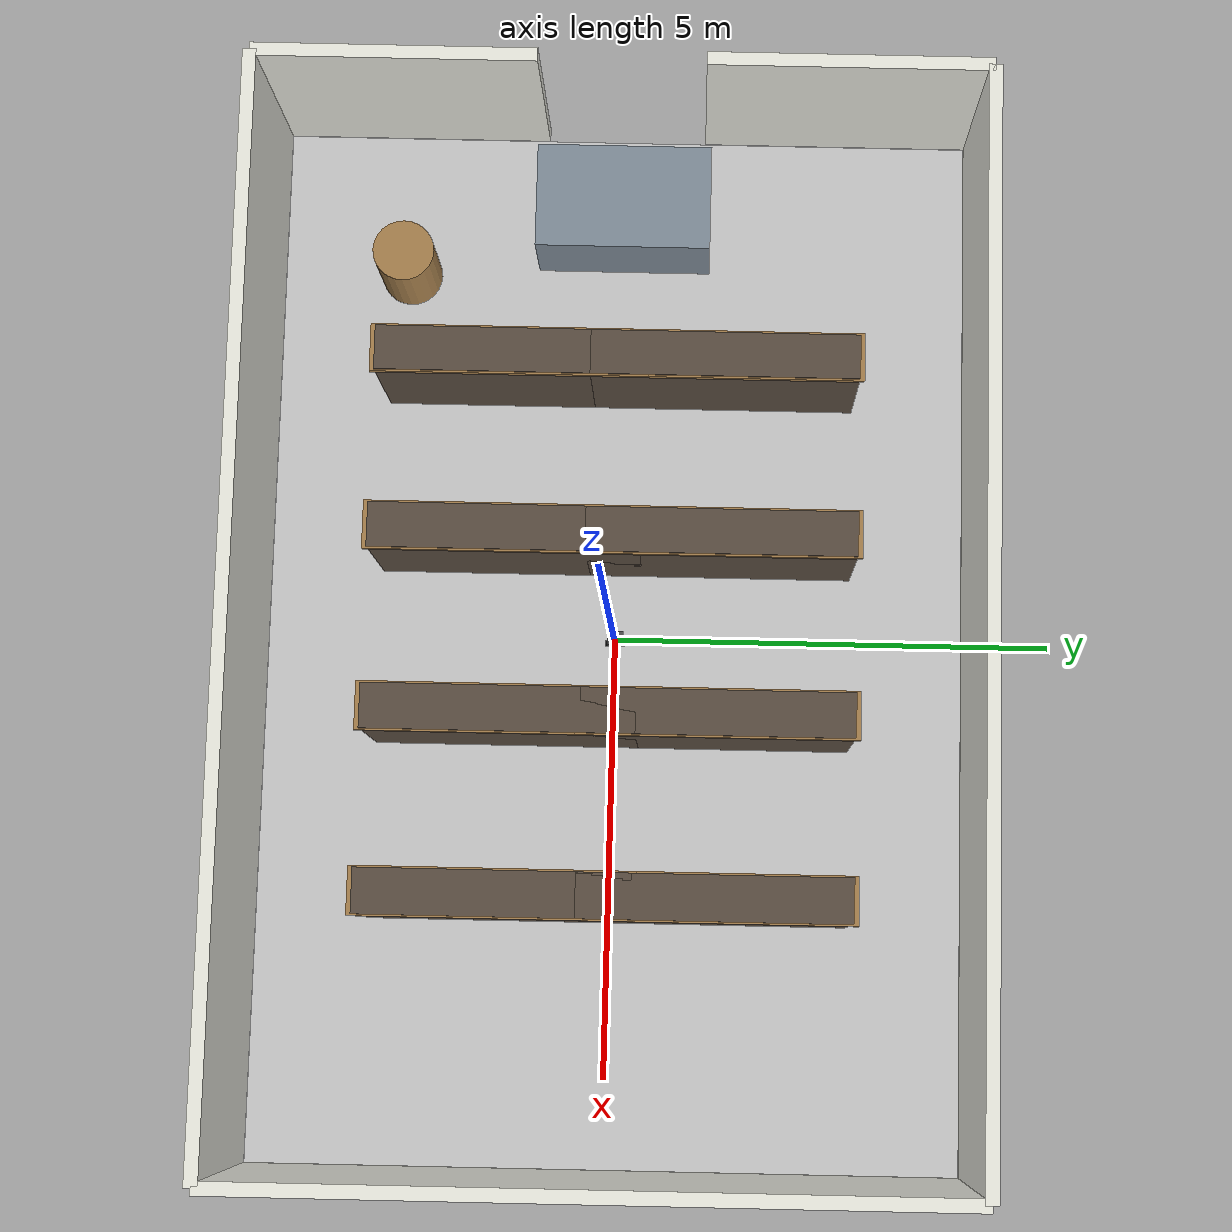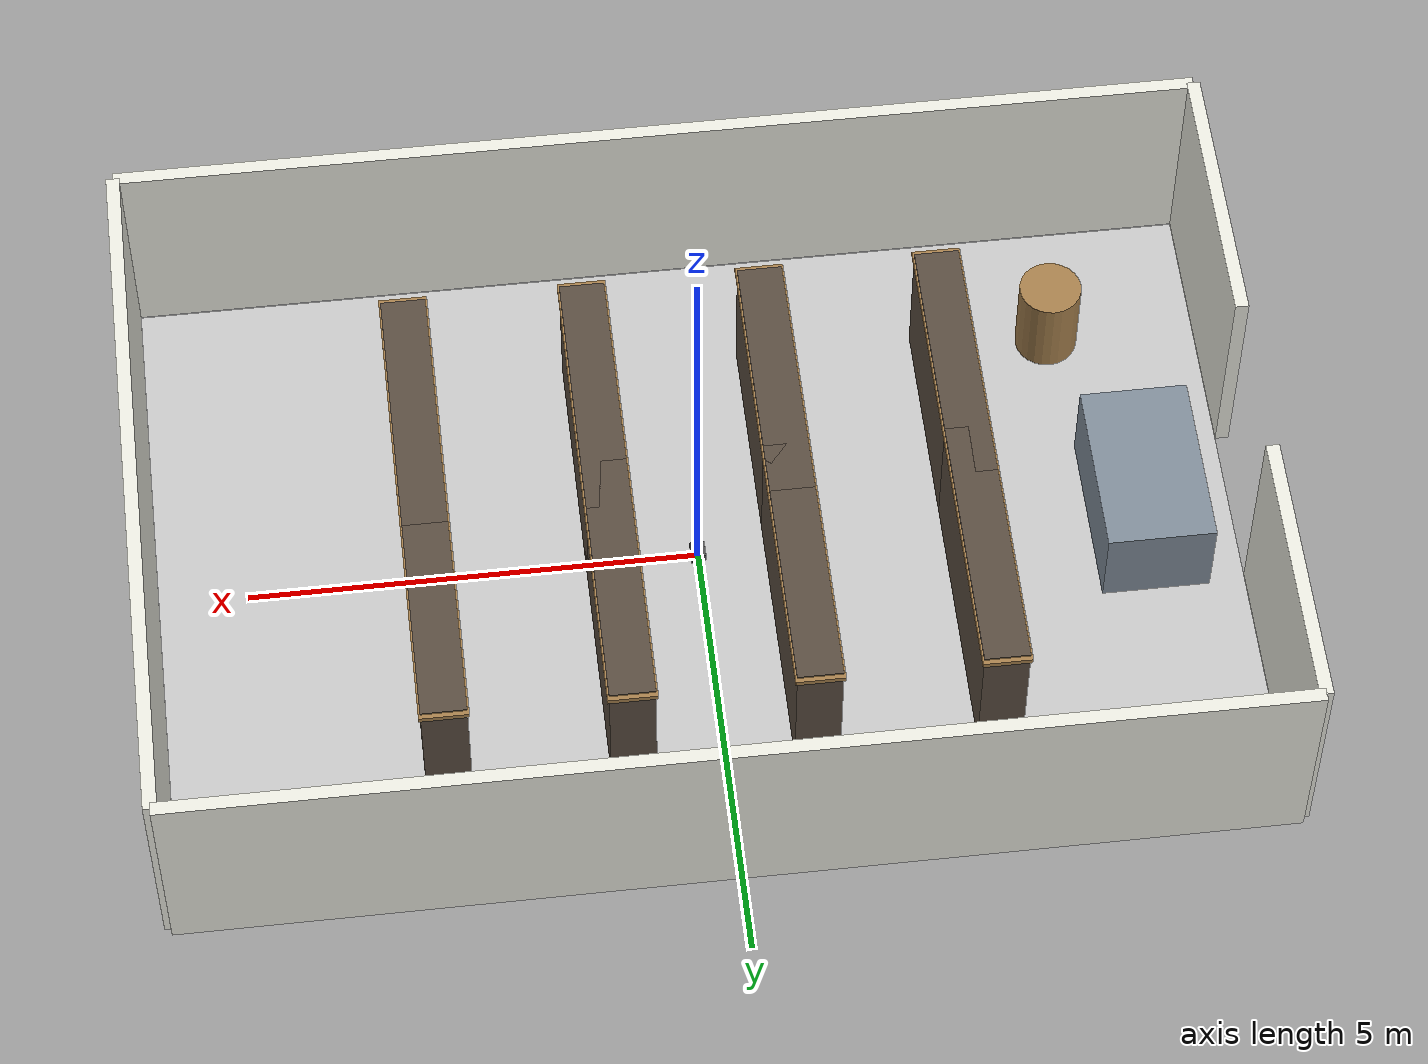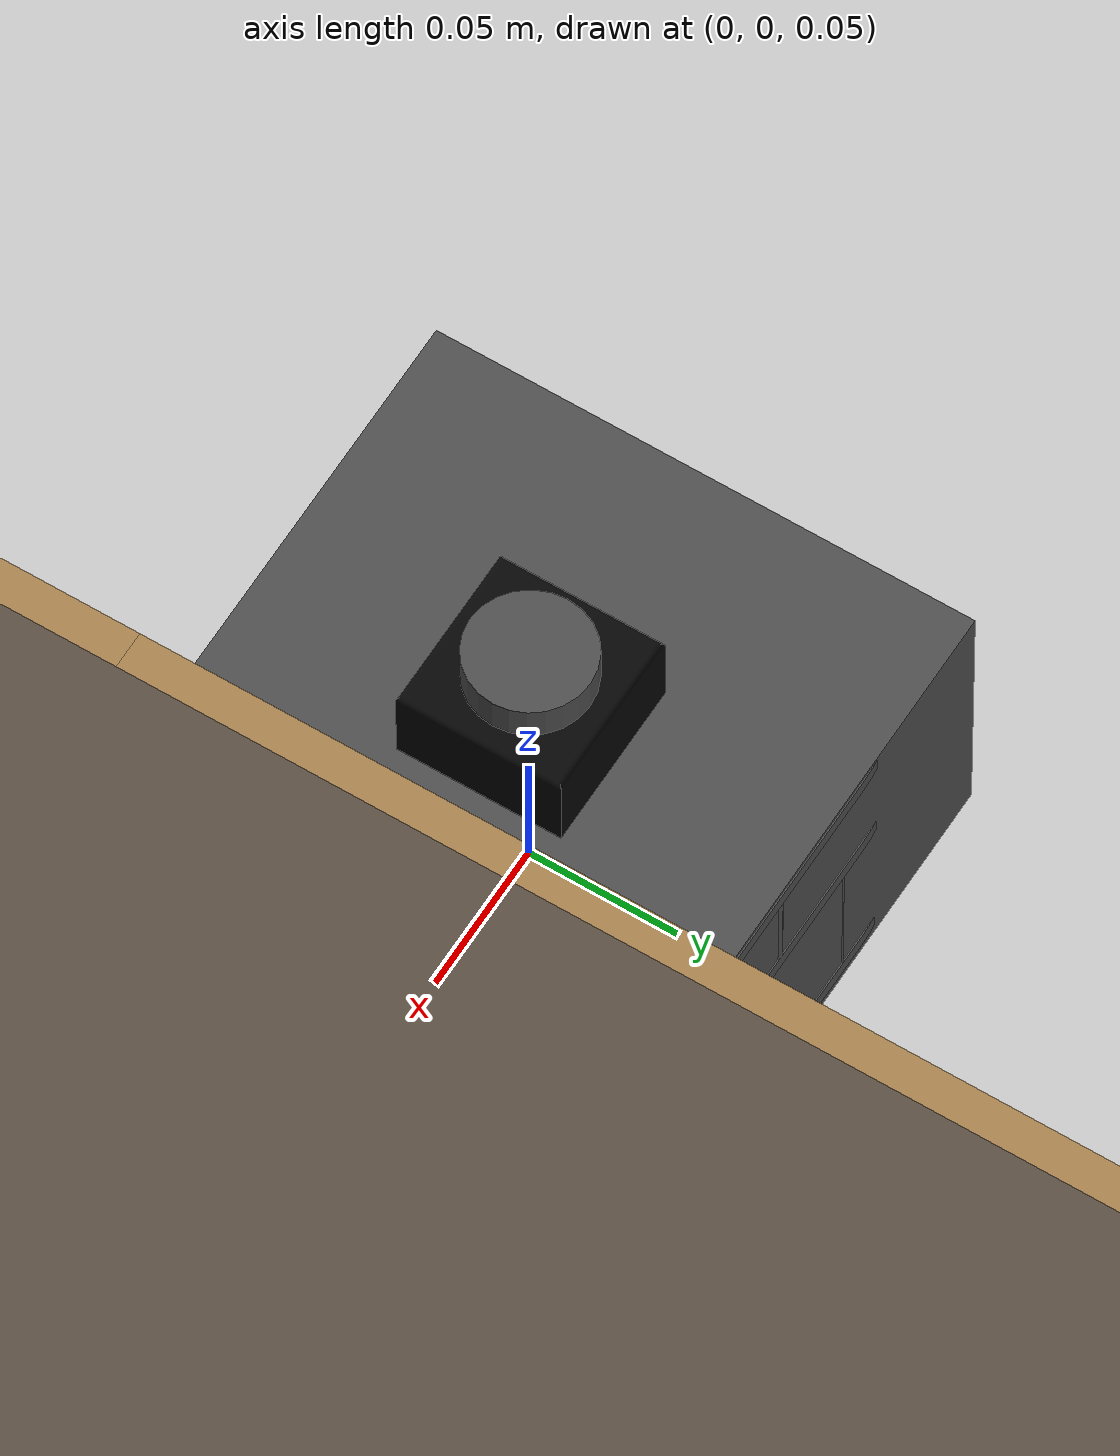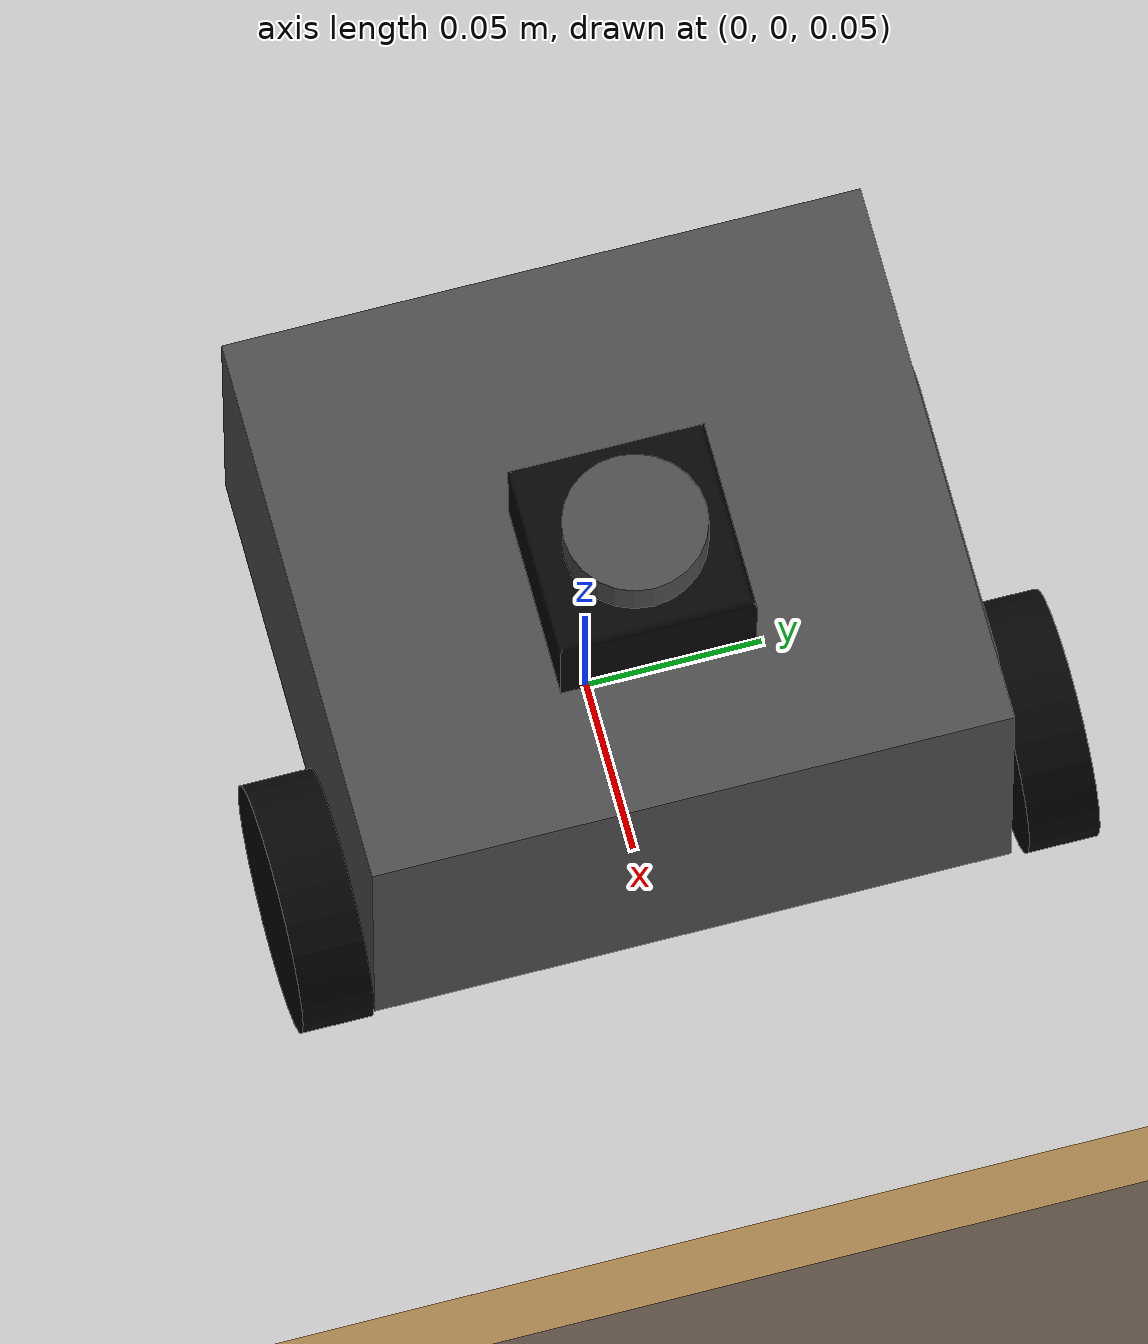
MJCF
<mujoco model="supermarket_scene">
  <include file="supermarket.xml"/>
  <compiler angle="radian" meshdir="."/>
  <option timestep="0.002" integrator="implicitfast"/>

  <asset>
    <mesh name="chassis_l1" file="../meshes/chassis_l1.stl" scale="0.001 0.001 0.001"/>
    <mesh name="chassis_l2" file="../meshes/chassis_l2.stl" scale="0.001 0.001 0.001"/>
    <mesh name="chassis_l3" file="../meshes/chassis_l3.stl" scale="0.001 0.001 0.001"/>
    <mesh name="wheel" file="../meshes/wheel.stl" scale="0.001 0.001 0.001"/>
    <mesh name="lidar_base_link" file="../meshes/lidar_base_link.stl" scale="0.001 0.001 0.001"/>
    <material name="gray" rgba="0.3 0.3 0.3 1"/>
    <material name="black" rgba="0.02 0.02 0.02 1"/>
    <material name="green" rgba="0 0.5 0 1"/>
  </asset>

  <default>
    <!-- 0.05 here costs 0.36 N*m at cruise (7 rad/s), more than the motors'
         whole torque budget; wheel bearings should be near-free -->
    <joint damping="0.001"/>
    <geom friction="0.9 0.01 0.001"/>
  </default>

  <worldbody>

    <!-- robot, spawned in the open cross-aisle at x=0 -->
    <body name="base_link" pos="0 0 0.04">
      <freejoint/>
      <inertial pos="0 0 0" mass="1.4" diaginertia="0.02 0.03 0.015"/>

      <geom type="mesh" mesh="chassis_l1" material="gray" contype="0" conaffinity="0" group="1"/>
      <geom type="mesh" mesh="chassis_l2" material="gray" contype="0" conaffinity="0" group="1"/>
      <geom type="mesh" mesh="chassis_l3" material="gray" contype="0" conaffinity="0" group="1"/>
      <geom type="box" size="0.080325 0.09 0.05" pos="0 0.009 0.066" material="gray"/>
      <!-- bottom at z=-0.001, level with the wheel contact plane (0.034-0.035);
           any lower and the robot tips onto it, unloads the wheels and hops -->
      <geom name="caster" type="sphere" size="0.012" pos="-0.064 0.0105 0.011" friction="0.05 0.005 0.0001"/>

      <geom type="mesh" mesh="lidar_base_link" material="black" pos="0 -9e-06 -0.000115" contype="0" conaffinity="0" group="1"/>
      <geom type="cylinder" size="0.02 0.0075" pos="0.015 0.01 0.15" material="gray" contype="0" conaffinity="0" group="1"/>
      <geom type="box" size="0.01 0.02 0.01" pos="0.06 0.005 0.09" material="green"/>

      <site name="lidar_ray_0" pos="0.015 0.01 0.15" zaxis="-1.000000 -0.000000 0"/>
      <site name="lidar_ray_1" pos="0.015 0.01 0.15" zaxis="-0.999848 -0.017452 0"/>
      <site name="lidar_ray_2" pos="0.015 0.01 0.15" zaxis="-0.999391 -0.034899 0"/>
      <site name="lidar_ray_3" pos="0.015 0.01 0.15" zaxis="-0.998630 -0.052336 0"/>
      <site name="lidar_ray_4" pos="0.015 0.01 0.15" zaxis="-0.997564 -0.069756 0"/>
      <site name="lidar_ray_5" pos="0.015 0.01 0.15" zaxis="-0.996195 -0.087156 0"/>
      <site name="lidar_ray_6" pos="0.015 0.01 0.15" zaxis="-0.994522 -0.104528 0"/>
      <site name="lidar_ray_7" pos="0.015 0.01 0.15" zaxis="-0.992546 -0.121869 0"/>
      <site name="lidar_ray_8" pos="0.015 0.01 0.15" zaxis="-0.990268 -0.139173 0"/>
      <site name="lidar_ray_9" pos="0.015 0.01 0.15" zaxis="-0.987688 -0.156434 0"/>
      <site name="lidar_ray_10" pos="0.015 0.01 0.15" zaxis="-0.984808 -0.173648 0"/>
      <site name="lidar_ray_11" pos="0.015 0.01 0.15" zaxis="-0.981627 -0.190809 0"/>
      <site name="lidar_ray_12" pos="0.015 0.01 0.15" zaxis="-0.978148 -0.207912 0"/>
      <site name="lidar_ray_13" pos="0.015 0.01 0.15" zaxis="-0.974370 -0.224951 0"/>
      <site name="lidar_ray_14" pos="0.015 0.01 0.15" zaxis="-0.970296 -0.241922 0"/>
      <site name="lidar_ray_15" pos="0.015 0.01 0.15" zaxis="-0.965926 -0.258819 0"/>
      <site name="lidar_ray_16" pos="0.015 0.01 0.15" zaxis="-0.961262 -0.275637 0"/>
      <site name="lidar_ray_17" pos="0.015 0.01 0.15" zaxis="-0.956305 -0.292372 0"/>
      <site name="lidar_ray_18" pos="0.015 0.01 0.15" zaxis="-0.951057 -0.309017 0"/>
      <site name="lidar_ray_19" pos="0.015 0.01 0.15" zaxis="-0.945519 -0.325568 0"/>
      <site name="lidar_ray_20" pos="0.015 0.01 0.15" zaxis="-0.939693 -0.342020 0"/>
      <site name="lidar_ray_21" pos="0.015 0.01 0.15" zaxis="-0.933580 -0.358368 0"/>
      <site name="lidar_ray_22" pos="0.015 0.01 0.15" zaxis="-0.927184 -0.374607 0"/>
      <site name="lidar_ray_23" pos="0.015 0.01 0.15" zaxis="-0.920505 -0.390731 0"/>
      <site name="lidar_ray_24" pos="0.015 0.01 0.15" zaxis="-0.913545 -0.406737 0"/>
      <site name="lidar_ray_25" pos="0.015 0.01 0.15" zaxis="-0.906308 -0.422618 0"/>
      <site name="lidar_ray_26" pos="0.015 0.01 0.15" zaxis="-0.898794 -0.438371 0"/>
      <site name="lidar_ray_27" pos="0.015 0.01 0.15" zaxis="-0.891007 -0.453990 0"/>
      <site name="lidar_ray_28" pos="0.015 0.01 0.15" zaxis="-0.882948 -0.469472 0"/>
      <site name="lidar_ray_29" pos="0.015 0.01 0.15" zaxis="-0.874620 -0.484810 0"/>
      <site name="lidar_ray_30" pos="0.015 0.01 0.15" zaxis="-0.866025 -0.500000 0"/>
      <site name="lidar_ray_31" pos="0.015 0.01 0.15" zaxis="-0.857167 -0.515038 0"/>
      <site name="lidar_ray_32" pos="0.015 0.01 0.15" zaxis="-0.848048 -0.529919 0"/>
      <site name="lidar_ray_33" pos="0.015 0.01 0.15" zaxis="-0.838671 -0.544639 0"/>
      <site name="lidar_ray_34" pos="0.015 0.01 0.15" zaxis="-0.829038 -0.559193 0"/>
      <site name="lidar_ray_35" pos="0.015 0.01 0.15" zaxis="-0.819152 -0.573576 0"/>
      <site name="lidar_ray_36" pos="0.015 0.01 0.15" zaxis="-0.809017 -0.587785 0"/>
      <site name="lidar_ray_37" pos="0.015 0.01 0.15" zaxis="-0.798636 -0.601815 0"/>
      <site name="lidar_ray_38" pos="0.015 0.01 0.15" zaxis="-0.788011 -0.615661 0"/>
      <site name="lidar_ray_39" pos="0.015 0.01 0.15" zaxis="-0.777146 -0.629320 0"/>
      <site name="lidar_ray_40" pos="0.015 0.01 0.15" zaxis="-0.766044 -0.642788 0"/>
      <site name="lidar_ray_41" pos="0.015 0.01 0.15" zaxis="-0.754710 -0.656059 0"/>
      <site name="lidar_ray_42" pos="0.015 0.01 0.15" zaxis="-0.743145 -0.669131 0"/>
      <site name="lidar_ray_43" pos="0.015 0.01 0.15" zaxis="-0.731354 -0.681998 0"/>
      <site name="lidar_ray_44" pos="0.015 0.01 0.15" zaxis="-0.719340 -0.694658 0"/>
      <site name="lidar_ray_45" pos="0.015 0.01 0.15" zaxis="-0.707107 -0.707107 0"/>
      <site name="lidar_ray_46" pos="0.015 0.01 0.15" zaxis="-0.694658 -0.719340 0"/>
      <site name="lidar_ray_47" pos="0.015 0.01 0.15" zaxis="-0.681998 -0.731354 0"/>
      <site name="lidar_ray_48" pos="0.015 0.01 0.15" zaxis="-0.669131 -0.743145 0"/>
      <site name="lidar_ray_49" pos="0.015 0.01 0.15" zaxis="-0.656059 -0.754710 0"/>
      <site name="lidar_ray_50" pos="0.015 0.01 0.15" zaxis="-0.642788 -0.766044 0"/>
      <site name="lidar_ray_51" pos="0.015 0.01 0.15" zaxis="-0.629320 -0.777146 0"/>
      <site name="lidar_ray_52" pos="0.015 0.01 0.15" zaxis="-0.615661 -0.788011 0"/>
      <site name="lidar_ray_53" pos="0.015 0.01 0.15" zaxis="-0.601815 -0.798636 0"/>
      <site name="lidar_ray_54" pos="0.015 0.01 0.15" zaxis="-0.587785 -0.809017 0"/>
      <site name="lidar_ray_55" pos="0.015 0.01 0.15" zaxis="-0.573576 -0.819152 0"/>
      <site name="lidar_ray_56" pos="0.015 0.01 0.15" zaxis="-0.559193 -0.829038 0"/>
      <site name="lidar_ray_57" pos="0.015 0.01 0.15" zaxis="-0.544639 -0.838671 0"/>
      <site name="lidar_ray_58" pos="0.015 0.01 0.15" zaxis="-0.529919 -0.848048 0"/>
      <site name="lidar_ray_59" pos="0.015 0.01 0.15" zaxis="-0.515038 -0.857167 0"/>
      <site name="lidar_ray_60" pos="0.015 0.01 0.15" zaxis="-0.500000 -0.866025 0"/>
      <site name="lidar_ray_61" pos="0.015 0.01 0.15" zaxis="-0.484810 -0.874620 0"/>
      <site name="lidar_ray_62" pos="0.015 0.01 0.15" zaxis="-0.469472 -0.882948 0"/>
      <site name="lidar_ray_63" pos="0.015 0.01 0.15" zaxis="-0.453990 -0.891007 0"/>
      <site name="lidar_ray_64" pos="0.015 0.01 0.15" zaxis="-0.438371 -0.898794 0"/>
      <site name="lidar_ray_65" pos="0.015 0.01 0.15" zaxis="-0.422618 -0.906308 0"/>
      <site name="lidar_ray_66" pos="0.015 0.01 0.15" zaxis="-0.406737 -0.913545 0"/>
      <site name="lidar_ray_67" pos="0.015 0.01 0.15" zaxis="-0.390731 -0.920505 0"/>
      <site name="lidar_ray_68" pos="0.015 0.01 0.15" zaxis="-0.374607 -0.927184 0"/>
      <site name="lidar_ray_69" pos="0.015 0.01 0.15" zaxis="-0.358368 -0.933580 0"/>
      <site name="lidar_ray_70" pos="0.015 0.01 0.15" zaxis="-0.342020 -0.939693 0"/>
      <site name="lidar_ray_71" pos="0.015 0.01 0.15" zaxis="-0.325568 -0.945519 0"/>
      <site name="lidar_ray_72" pos="0.015 0.01 0.15" zaxis="-0.309017 -0.951057 0"/>
      <site name="lidar_ray_73" pos="0.015 0.01 0.15" zaxis="-0.292372 -0.956305 0"/>
      <site name="lidar_ray_74" pos="0.015 0.01 0.15" zaxis="-0.275637 -0.961262 0"/>
      <site name="lidar_ray_75" pos="0.015 0.01 0.15" zaxis="-0.258819 -0.965926 0"/>
      <site name="lidar_ray_76" pos="0.015 0.01 0.15" zaxis="-0.241922 -0.970296 0"/>
      <site name="lidar_ray_77" pos="0.015 0.01 0.15" zaxis="-0.224951 -0.974370 0"/>
      <site name="lidar_ray_78" pos="0.015 0.01 0.15" zaxis="-0.207912 -0.978148 0"/>
      <site name="lidar_ray_79" pos="0.015 0.01 0.15" zaxis="-0.190809 -0.981627 0"/>
      <site name="lidar_ray_80" pos="0.015 0.01 0.15" zaxis="-0.173648 -0.984808 0"/>
      <site name="lidar_ray_81" pos="0.015 0.01 0.15" zaxis="-0.156434 -0.987688 0"/>
      <site name="lidar_ray_82" pos="0.015 0.01 0.15" zaxis="-0.139173 -0.990268 0"/>
      <site name="lidar_ray_83" pos="0.015 0.01 0.15" zaxis="-0.121869 -0.992546 0"/>
      <site name="lidar_ray_84" pos="0.015 0.01 0.15" zaxis="-0.104528 -0.994522 0"/>
      <site name="lidar_ray_85" pos="0.015 0.01 0.15" zaxis="-0.087156 -0.996195 0"/>
      <site name="lidar_ray_86" pos="0.015 0.01 0.15" zaxis="-0.069756 -0.997564 0"/>
      <site name="lidar_ray_87" pos="0.015 0.01 0.15" zaxis="-0.052336 -0.998630 0"/>
      <site name="lidar_ray_88" pos="0.015 0.01 0.15" zaxis="-0.034899 -0.999391 0"/>
      <site name="lidar_ray_89" pos="0.015 0.01 0.15" zaxis="-0.017452 -0.999848 0"/>
      <site name="lidar_ray_90" pos="0.015 0.01 0.15" zaxis="0.000000 -1.000000 0"/>
      <site name="lidar_ray_91" pos="0.015 0.01 0.15" zaxis="0.017452 -0.999848 0"/>
      <site name="lidar_ray_92" pos="0.015 0.01 0.15" zaxis="0.034899 -0.999391 0"/>
      <site name="lidar_ray_93" pos="0.015 0.01 0.15" zaxis="0.052336 -0.998630 0"/>
      <site name="lidar_ray_94" pos="0.015 0.01 0.15" zaxis="0.069756 -0.997564 0"/>
      <site name="lidar_ray_95" pos="0.015 0.01 0.15" zaxis="0.087156 -0.996195 0"/>
      <site name="lidar_ray_96" pos="0.015 0.01 0.15" zaxis="0.104528 -0.994522 0"/>
      <site name="lidar_ray_97" pos="0.015 0.01 0.15" zaxis="0.121869 -0.992546 0"/>
      <site name="lidar_ray_98" pos="0.015 0.01 0.15" zaxis="0.139173 -0.990268 0"/>
      <site name="lidar_ray_99" pos="0.015 0.01 0.15" zaxis="0.156434 -0.987688 0"/>
      <site name="lidar_ray_100" pos="0.015 0.01 0.15" zaxis="0.173648 -0.984808 0"/>
      <site name="lidar_ray_101" pos="0.015 0.01 0.15" zaxis="0.190809 -0.981627 0"/>
      <site name="lidar_ray_102" pos="0.015 0.01 0.15" zaxis="0.207912 -0.978148 0"/>
      <site name="lidar_ray_103" pos="0.015 0.01 0.15" zaxis="0.224951 -0.974370 0"/>
      <site name="lidar_ray_104" pos="0.015 0.01 0.15" zaxis="0.241922 -0.970296 0"/>
      <site name="lidar_ray_105" pos="0.015 0.01 0.15" zaxis="0.258819 -0.965926 0"/>
      <site name="lidar_ray_106" pos="0.015 0.01 0.15" zaxis="0.275637 -0.961262 0"/>
      <site name="lidar_ray_107" pos="0.015 0.01 0.15" zaxis="0.292372 -0.956305 0"/>
      <site name="lidar_ray_108" pos="0.015 0.01 0.15" zaxis="0.309017 -0.951057 0"/>
      <site name="lidar_ray_109" pos="0.015 0.01 0.15" zaxis="0.325568 -0.945519 0"/>
      <site name="lidar_ray_110" pos="0.015 0.01 0.15" zaxis="0.342020 -0.939693 0"/>
      <site name="lidar_ray_111" pos="0.015 0.01 0.15" zaxis="0.358368 -0.933580 0"/>
      <site name="lidar_ray_112" pos="0.015 0.01 0.15" zaxis="0.374607 -0.927184 0"/>
      <site name="lidar_ray_113" pos="0.015 0.01 0.15" zaxis="0.390731 -0.920505 0"/>
      <site name="lidar_ray_114" pos="0.015 0.01 0.15" zaxis="0.406737 -0.913545 0"/>
      <site name="lidar_ray_115" pos="0.015 0.01 0.15" zaxis="0.422618 -0.906308 0"/>
      <site name="lidar_ray_116" pos="0.015 0.01 0.15" zaxis="0.438371 -0.898794 0"/>
      <site name="lidar_ray_117" pos="0.015 0.01 0.15" zaxis="0.453990 -0.891007 0"/>
      <site name="lidar_ray_118" pos="0.015 0.01 0.15" zaxis="0.469472 -0.882948 0"/>
      <site name="lidar_ray_119" pos="0.015 0.01 0.15" zaxis="0.484810 -0.874620 0"/>
      <site name="lidar_ray_120" pos="0.015 0.01 0.15" zaxis="0.500000 -0.866025 0"/>
      <site name="lidar_ray_121" pos="0.015 0.01 0.15" zaxis="0.515038 -0.857167 0"/>
      <site name="lidar_ray_122" pos="0.015 0.01 0.15" zaxis="0.529919 -0.848048 0"/>
      <site name="lidar_ray_123" pos="0.015 0.01 0.15" zaxis="0.544639 -0.838671 0"/>
      <site name="lidar_ray_124" pos="0.015 0.01 0.15" zaxis="0.559193 -0.829038 0"/>
      <site name="lidar_ray_125" pos="0.015 0.01 0.15" zaxis="0.573576 -0.819152 0"/>
      <site name="lidar_ray_126" pos="0.015 0.01 0.15" zaxis="0.587785 -0.809017 0"/>
      <site name="lidar_ray_127" pos="0.015 0.01 0.15" zaxis="0.601815 -0.798636 0"/>
      <site name="lidar_ray_128" pos="0.015 0.01 0.15" zaxis="0.615661 -0.788011 0"/>
      <site name="lidar_ray_129" pos="0.015 0.01 0.15" zaxis="0.629320 -0.777146 0"/>
      <site name="lidar_ray_130" pos="0.015 0.01 0.15" zaxis="0.642788 -0.766044 0"/>
      <site name="lidar_ray_131" pos="0.015 0.01 0.15" zaxis="0.656059 -0.754710 0"/>
      <site name="lidar_ray_132" pos="0.015 0.01 0.15" zaxis="0.669131 -0.743145 0"/>
      <site name="lidar_ray_133" pos="0.015 0.01 0.15" zaxis="0.681998 -0.731354 0"/>
      <site name="lidar_ray_134" pos="0.015 0.01 0.15" zaxis="0.694658 -0.719340 0"/>
      <site name="lidar_ray_135" pos="0.015 0.01 0.15" zaxis="0.707107 -0.707107 0"/>
      <site name="lidar_ray_136" pos="0.015 0.01 0.15" zaxis="0.719340 -0.694658 0"/>
      <site name="lidar_ray_137" pos="0.015 0.01 0.15" zaxis="0.731354 -0.681998 0"/>
      <site name="lidar_ray_138" pos="0.015 0.01 0.15" zaxis="0.743145 -0.669131 0"/>
      <site name="lidar_ray_139" pos="0.015 0.01 0.15" zaxis="0.754710 -0.656059 0"/>
      <site name="lidar_ray_140" pos="0.015 0.01 0.15" zaxis="0.766044 -0.642788 0"/>
      <site name="lidar_ray_141" pos="0.015 0.01 0.15" zaxis="0.777146 -0.629320 0"/>
      <site name="lidar_ray_142" pos="0.015 0.01 0.15" zaxis="0.788011 -0.615661 0"/>
      <site name="lidar_ray_143" pos="0.015 0.01 0.15" zaxis="0.798636 -0.601815 0"/>
      <site name="lidar_ray_144" pos="0.015 0.01 0.15" zaxis="0.809017 -0.587785 0"/>
      <site name="lidar_ray_145" pos="0.015 0.01 0.15" zaxis="0.819152 -0.573576 0"/>
      <site name="lidar_ray_146" pos="0.015 0.01 0.15" zaxis="0.829038 -0.559193 0"/>
      <site name="lidar_ray_147" pos="0.015 0.01 0.15" zaxis="0.838671 -0.544639 0"/>
      <site name="lidar_ray_148" pos="0.015 0.01 0.15" zaxis="0.848048 -0.529919 0"/>
      <site name="lidar_ray_149" pos="0.015 0.01 0.15" zaxis="0.857167 -0.515038 0"/>
      <site name="lidar_ray_150" pos="0.015 0.01 0.15" zaxis="0.866025 -0.500000 0"/>
      <site name="lidar_ray_151" pos="0.015 0.01 0.15" zaxis="0.874620 -0.484810 0"/>
      <site name="lidar_ray_152" pos="0.015 0.01 0.15" zaxis="0.882948 -0.469472 0"/>
      <site name="lidar_ray_153" pos="0.015 0.01 0.15" zaxis="0.891007 -0.453990 0"/>
      <site name="lidar_ray_154" pos="0.015 0.01 0.15" zaxis="0.898794 -0.438371 0"/>
      <site name="lidar_ray_155" pos="0.015 0.01 0.15" zaxis="0.906308 -0.422618 0"/>
      <site name="lidar_ray_156" pos="0.015 0.01 0.15" zaxis="0.913545 -0.406737 0"/>
      <site name="lidar_ray_157" pos="0.015 0.01 0.15" zaxis="0.920505 -0.390731 0"/>
      <site name="lidar_ray_158" pos="0.015 0.01 0.15" zaxis="0.927184 -0.374607 0"/>
      <site name="lidar_ray_159" pos="0.015 0.01 0.15" zaxis="0.933580 -0.358368 0"/>
      <site name="lidar_ray_160" pos="0.015 0.01 0.15" zaxis="0.939693 -0.342020 0"/>
      <site name="lidar_ray_161" pos="0.015 0.01 0.15" zaxis="0.945519 -0.325568 0"/>
      <site name="lidar_ray_162" pos="0.015 0.01 0.15" zaxis="0.951057 -0.309017 0"/>
      <site name="lidar_ray_163" pos="0.015 0.01 0.15" zaxis="0.956305 -0.292372 0"/>
      <site name="lidar_ray_164" pos="0.015 0.01 0.15" zaxis="0.961262 -0.275637 0"/>
      <site name="lidar_ray_165" pos="0.015 0.01 0.15" zaxis="0.965926 -0.258819 0"/>
      <site name="lidar_ray_166" pos="0.015 0.01 0.15" zaxis="0.970296 -0.241922 0"/>
      <site name="lidar_ray_167" pos="0.015 0.01 0.15" zaxis="0.974370 -0.224951 0"/>
      <site name="lidar_ray_168" pos="0.015 0.01 0.15" zaxis="0.978148 -0.207912 0"/>
      <site name="lidar_ray_169" pos="0.015 0.01 0.15" zaxis="0.981627 -0.190809 0"/>
      <site name="lidar_ray_170" pos="0.015 0.01 0.15" zaxis="0.984808 -0.173648 0"/>
      <site name="lidar_ray_171" pos="0.015 0.01 0.15" zaxis="0.987688 -0.156434 0"/>
      <site name="lidar_ray_172" pos="0.015 0.01 0.15" zaxis="0.990268 -0.139173 0"/>
      <site name="lidar_ray_173" pos="0.015 0.01 0.15" zaxis="0.992546 -0.121869 0"/>
      <site name="lidar_ray_174" pos="0.015 0.01 0.15" zaxis="0.994522 -0.104528 0"/>
      <site name="lidar_ray_175" pos="0.015 0.01 0.15" zaxis="0.996195 -0.087156 0"/>
      <site name="lidar_ray_176" pos="0.015 0.01 0.15" zaxis="0.997564 -0.069756 0"/>
      <site name="lidar_ray_177" pos="0.015 0.01 0.15" zaxis="0.998630 -0.052336 0"/>
      <site name="lidar_ray_178" pos="0.015 0.01 0.15" zaxis="0.999391 -0.034899 0"/>
      <site name="lidar_ray_179" pos="0.015 0.01 0.15" zaxis="0.999848 -0.017452 0"/>
      <site name="lidar_ray_180" pos="0.015 0.01 0.15" zaxis="1.000000 0.000000 0"/>
      <site name="lidar_ray_181" pos="0.015 0.01 0.15" zaxis="0.999848 0.017452 0"/>
      <site name="lidar_ray_182" pos="0.015 0.01 0.15" zaxis="0.999391 0.034899 0"/>
      <site name="lidar_ray_183" pos="0.015 0.01 0.15" zaxis="0.998630 0.052336 0"/>
      <site name="lidar_ray_184" pos="0.015 0.01 0.15" zaxis="0.997564 0.069756 0"/>
      <site name="lidar_ray_185" pos="0.015 0.01 0.15" zaxis="0.996195 0.087156 0"/>
      <site name="lidar_ray_186" pos="0.015 0.01 0.15" zaxis="0.994522 0.104528 0"/>
      <site name="lidar_ray_187" pos="0.015 0.01 0.15" zaxis="0.992546 0.121869 0"/>
      <site name="lidar_ray_188" pos="0.015 0.01 0.15" zaxis="0.990268 0.139173 0"/>
      <site name="lidar_ray_189" pos="0.015 0.01 0.15" zaxis="0.987688 0.156434 0"/>
      <site name="lidar_ray_190" pos="0.015 0.01 0.15" zaxis="0.984808 0.173648 0"/>
      <site name="lidar_ray_191" pos="0.015 0.01 0.15" zaxis="0.981627 0.190809 0"/>
      <site name="lidar_ray_192" pos="0.015 0.01 0.15" zaxis="0.978148 0.207912 0"/>
      <site name="lidar_ray_193" pos="0.015 0.01 0.15" zaxis="0.974370 0.224951 0"/>
      <site name="lidar_ray_194" pos="0.015 0.01 0.15" zaxis="0.970296 0.241922 0"/>
      <site name="lidar_ray_195" pos="0.015 0.01 0.15" zaxis="0.965926 0.258819 0"/>
      <site name="lidar_ray_196" pos="0.015 0.01 0.15" zaxis="0.961262 0.275637 0"/>
      <site name="lidar_ray_197" pos="0.015 0.01 0.15" zaxis="0.956305 0.292372 0"/>
      <site name="lidar_ray_198" pos="0.015 0.01 0.15" zaxis="0.951057 0.309017 0"/>
      <site name="lidar_ray_199" pos="0.015 0.01 0.15" zaxis="0.945519 0.325568 0"/>
      <site name="lidar_ray_200" pos="0.015 0.01 0.15" zaxis="0.939693 0.342020 0"/>
      <site name="lidar_ray_201" pos="0.015 0.01 0.15" zaxis="0.933580 0.358368 0"/>
      <site name="lidar_ray_202" pos="0.015 0.01 0.15" zaxis="0.927184 0.374607 0"/>
      <site name="lidar_ray_203" pos="0.015 0.01 0.15" zaxis="0.920505 0.390731 0"/>
      <site name="lidar_ray_204" pos="0.015 0.01 0.15" zaxis="0.913545 0.406737 0"/>
      <site name="lidar_ray_205" pos="0.015 0.01 0.15" zaxis="0.906308 0.422618 0"/>
      <site name="lidar_ray_206" pos="0.015 0.01 0.15" zaxis="0.898794 0.438371 0"/>
      <site name="lidar_ray_207" pos="0.015 0.01 0.15" zaxis="0.891007 0.453990 0"/>
      <site name="lidar_ray_208" pos="0.015 0.01 0.15" zaxis="0.882948 0.469472 0"/>
      <site name="lidar_ray_209" pos="0.015 0.01 0.15" zaxis="0.874620 0.484810 0"/>
      <site name="lidar_ray_210" pos="0.015 0.01 0.15" zaxis="0.866025 0.500000 0"/>
      <site name="lidar_ray_211" pos="0.015 0.01 0.15" zaxis="0.857167 0.515038 0"/>
      <site name="lidar_ray_212" pos="0.015 0.01 0.15" zaxis="0.848048 0.529919 0"/>
      <site name="lidar_ray_213" pos="0.015 0.01 0.15" zaxis="0.838671 0.544639 0"/>
      <site name="lidar_ray_214" pos="0.015 0.01 0.15" zaxis="0.829038 0.559193 0"/>
      <site name="lidar_ray_215" pos="0.015 0.01 0.15" zaxis="0.819152 0.573576 0"/>
      <site name="lidar_ray_216" pos="0.015 0.01 0.15" zaxis="0.809017 0.587785 0"/>
      <site name="lidar_ray_217" pos="0.015 0.01 0.15" zaxis="0.798636 0.601815 0"/>
      <site name="lidar_ray_218" pos="0.015 0.01 0.15" zaxis="0.788011 0.615661 0"/>
      <site name="lidar_ray_219" pos="0.015 0.01 0.15" zaxis="0.777146 0.629320 0"/>
      <site name="lidar_ray_220" pos="0.015 0.01 0.15" zaxis="0.766044 0.642788 0"/>
      <site name="lidar_ray_221" pos="0.015 0.01 0.15" zaxis="0.754710 0.656059 0"/>
      <site name="lidar_ray_222" pos="0.015 0.01 0.15" zaxis="0.743145 0.669131 0"/>
      <site name="lidar_ray_223" pos="0.015 0.01 0.15" zaxis="0.731354 0.681998 0"/>
      <site name="lidar_ray_224" pos="0.015 0.01 0.15" zaxis="0.719340 0.694658 0"/>
      <site name="lidar_ray_225" pos="0.015 0.01 0.15" zaxis="0.707107 0.707107 0"/>
      <site name="lidar_ray_226" pos="0.015 0.01 0.15" zaxis="0.694658 0.719340 0"/>
      <site name="lidar_ray_227" pos="0.015 0.01 0.15" zaxis="0.681998 0.731354 0"/>
      <site name="lidar_ray_228" pos="0.015 0.01 0.15" zaxis="0.669131 0.743145 0"/>
      <site name="lidar_ray_229" pos="0.015 0.01 0.15" zaxis="0.656059 0.754710 0"/>
      <site name="lidar_ray_230" pos="0.015 0.01 0.15" zaxis="0.642788 0.766044 0"/>
      <site name="lidar_ray_231" pos="0.015 0.01 0.15" zaxis="0.629320 0.777146 0"/>
      <site name="lidar_ray_232" pos="0.015 0.01 0.15" zaxis="0.615661 0.788011 0"/>
      <site name="lidar_ray_233" pos="0.015 0.01 0.15" zaxis="0.601815 0.798636 0"/>
      <site name="lidar_ray_234" pos="0.015 0.01 0.15" zaxis="0.587785 0.809017 0"/>
      <site name="lidar_ray_235" pos="0.015 0.01 0.15" zaxis="0.573576 0.819152 0"/>
      <site name="lidar_ray_236" pos="0.015 0.01 0.15" zaxis="0.559193 0.829038 0"/>
      <site name="lidar_ray_237" pos="0.015 0.01 0.15" zaxis="0.544639 0.838671 0"/>
      <site name="lidar_ray_238" pos="0.015 0.01 0.15" zaxis="0.529919 0.848048 0"/>
      <site name="lidar_ray_239" pos="0.015 0.01 0.15" zaxis="0.515038 0.857167 0"/>
      <site name="lidar_ray_240" pos="0.015 0.01 0.15" zaxis="0.500000 0.866025 0"/>
      <site name="lidar_ray_241" pos="0.015 0.01 0.15" zaxis="0.484810 0.874620 0"/>
      <site name="lidar_ray_242" pos="0.015 0.01 0.15" zaxis="0.469472 0.882948 0"/>
      <site name="lidar_ray_243" pos="0.015 0.01 0.15" zaxis="0.453990 0.891007 0"/>
      <site name="lidar_ray_244" pos="0.015 0.01 0.15" zaxis="0.438371 0.898794 0"/>
      <site name="lidar_ray_245" pos="0.015 0.01 0.15" zaxis="0.422618 0.906308 0"/>
      <site name="lidar_ray_246" pos="0.015 0.01 0.15" zaxis="0.406737 0.913545 0"/>
      <site name="lidar_ray_247" pos="0.015 0.01 0.15" zaxis="0.390731 0.920505 0"/>
      <site name="lidar_ray_248" pos="0.015 0.01 0.15" zaxis="0.374607 0.927184 0"/>
      <site name="lidar_ray_249" pos="0.015 0.01 0.15" zaxis="0.358368 0.933580 0"/>
      <site name="lidar_ray_250" pos="0.015 0.01 0.15" zaxis="0.342020 0.939693 0"/>
      <site name="lidar_ray_251" pos="0.015 0.01 0.15" zaxis="0.325568 0.945519 0"/>
      <site name="lidar_ray_252" pos="0.015 0.01 0.15" zaxis="0.309017 0.951057 0"/>
      <site name="lidar_ray_253" pos="0.015 0.01 0.15" zaxis="0.292372 0.956305 0"/>
      <site name="lidar_ray_254" pos="0.015 0.01 0.15" zaxis="0.275637 0.961262 0"/>
      <site name="lidar_ray_255" pos="0.015 0.01 0.15" zaxis="0.258819 0.965926 0"/>
      <site name="lidar_ray_256" pos="0.015 0.01 0.15" zaxis="0.241922 0.970296 0"/>
      <site name="lidar_ray_257" pos="0.015 0.01 0.15" zaxis="0.224951 0.974370 0"/>
      <site name="lidar_ray_258" pos="0.015 0.01 0.15" zaxis="0.207912 0.978148 0"/>
      <site name="lidar_ray_259" pos="0.015 0.01 0.15" zaxis="0.190809 0.981627 0"/>
      <site name="lidar_ray_260" pos="0.015 0.01 0.15" zaxis="0.173648 0.984808 0"/>
      <site name="lidar_ray_261" pos="0.015 0.01 0.15" zaxis="0.156434 0.987688 0"/>
      <site name="lidar_ray_262" pos="0.015 0.01 0.15" zaxis="0.139173 0.990268 0"/>
      <site name="lidar_ray_263" pos="0.015 0.01 0.15" zaxis="0.121869 0.992546 0"/>
      <site name="lidar_ray_264" pos="0.015 0.01 0.15" zaxis="0.104528 0.994522 0"/>
      <site name="lidar_ray_265" pos="0.015 0.01 0.15" zaxis="0.087156 0.996195 0"/>
      <site name="lidar_ray_266" pos="0.015 0.01 0.15" zaxis="0.069756 0.997564 0"/>
      <site name="lidar_ray_267" pos="0.015 0.01 0.15" zaxis="0.052336 0.998630 0"/>
      <site name="lidar_ray_268" pos="0.015 0.01 0.15" zaxis="0.034899 0.999391 0"/>
      <site name="lidar_ray_269" pos="0.015 0.01 0.15" zaxis="0.017452 0.999848 0"/>
      <site name="lidar_ray_270" pos="0.015 0.01 0.15" zaxis="0.000000 1.000000 0"/>
      <site name="lidar_ray_271" pos="0.015 0.01 0.15" zaxis="-0.017452 0.999848 0"/>
      <site name="lidar_ray_272" pos="0.015 0.01 0.15" zaxis="-0.034899 0.999391 0"/>
      <site name="lidar_ray_273" pos="0.015 0.01 0.15" zaxis="-0.052336 0.998630 0"/>
      <site name="lidar_ray_274" pos="0.015 0.01 0.15" zaxis="-0.069756 0.997564 0"/>
      <site name="lidar_ray_275" pos="0.015 0.01 0.15" zaxis="-0.087156 0.996195 0"/>
      <site name="lidar_ray_276" pos="0.015 0.01 0.15" zaxis="-0.104528 0.994522 0"/>
      <site name="lidar_ray_277" pos="0.015 0.01 0.15" zaxis="-0.121869 0.992546 0"/>
      <site name="lidar_ray_278" pos="0.015 0.01 0.15" zaxis="-0.139173 0.990268 0"/>
      <site name="lidar_ray_279" pos="0.015 0.01 0.15" zaxis="-0.156434 0.987688 0"/>
      <site name="lidar_ray_280" pos="0.015 0.01 0.15" zaxis="-0.173648 0.984808 0"/>
      <site name="lidar_ray_281" pos="0.015 0.01 0.15" zaxis="-0.190809 0.981627 0"/>
      <site name="lidar_ray_282" pos="0.015 0.01 0.15" zaxis="-0.207912 0.978148 0"/>
      <site name="lidar_ray_283" pos="0.015 0.01 0.15" zaxis="-0.224951 0.974370 0"/>
      <site name="lidar_ray_284" pos="0.015 0.01 0.15" zaxis="-0.241922 0.970296 0"/>
      <site name="lidar_ray_285" pos="0.015 0.01 0.15" zaxis="-0.258819 0.965926 0"/>
      <site name="lidar_ray_286" pos="0.015 0.01 0.15" zaxis="-0.275637 0.961262 0"/>
      <site name="lidar_ray_287" pos="0.015 0.01 0.15" zaxis="-0.292372 0.956305 0"/>
      <site name="lidar_ray_288" pos="0.015 0.01 0.15" zaxis="-0.309017 0.951057 0"/>
      <site name="lidar_ray_289" pos="0.015 0.01 0.15" zaxis="-0.325568 0.945519 0"/>
      <site name="lidar_ray_290" pos="0.015 0.01 0.15" zaxis="-0.342020 0.939693 0"/>
      <site name="lidar_ray_291" pos="0.015 0.01 0.15" zaxis="-0.358368 0.933580 0"/>
      <site name="lidar_ray_292" pos="0.015 0.01 0.15" zaxis="-0.374607 0.927184 0"/>
      <site name="lidar_ray_293" pos="0.015 0.01 0.15" zaxis="-0.390731 0.920505 0"/>
      <site name="lidar_ray_294" pos="0.015 0.01 0.15" zaxis="-0.406737 0.913545 0"/>
      <site name="lidar_ray_295" pos="0.015 0.01 0.15" zaxis="-0.422618 0.906308 0"/>
      <site name="lidar_ray_296" pos="0.015 0.01 0.15" zaxis="-0.438371 0.898794 0"/>
      <site name="lidar_ray_297" pos="0.015 0.01 0.15" zaxis="-0.453990 0.891007 0"/>
      <site name="lidar_ray_298" pos="0.015 0.01 0.15" zaxis="-0.469472 0.882948 0"/>
      <site name="lidar_ray_299" pos="0.015 0.01 0.15" zaxis="-0.484810 0.874620 0"/>
      <site name="lidar_ray_300" pos="0.015 0.01 0.15" zaxis="-0.500000 0.866025 0"/>
      <site name="lidar_ray_301" pos="0.015 0.01 0.15" zaxis="-0.515038 0.857167 0"/>
      <site name="lidar_ray_302" pos="0.015 0.01 0.15" zaxis="-0.529919 0.848048 0"/>
      <site name="lidar_ray_303" pos="0.015 0.01 0.15" zaxis="-0.544639 0.838671 0"/>
      <site name="lidar_ray_304" pos="0.015 0.01 0.15" zaxis="-0.559193 0.829038 0"/>
      <site name="lidar_ray_305" pos="0.015 0.01 0.15" zaxis="-0.573576 0.819152 0"/>
      <site name="lidar_ray_306" pos="0.015 0.01 0.15" zaxis="-0.587785 0.809017 0"/>
      <site name="lidar_ray_307" pos="0.015 0.01 0.15" zaxis="-0.601815 0.798636 0"/>
      <site name="lidar_ray_308" pos="0.015 0.01 0.15" zaxis="-0.615661 0.788011 0"/>
      <site name="lidar_ray_309" pos="0.015 0.01 0.15" zaxis="-0.629320 0.777146 0"/>
      <site name="lidar_ray_310" pos="0.015 0.01 0.15" zaxis="-0.642788 0.766044 0"/>
      <site name="lidar_ray_311" pos="0.015 0.01 0.15" zaxis="-0.656059 0.754710 0"/>
      <site name="lidar_ray_312" pos="0.015 0.01 0.15" zaxis="-0.669131 0.743145 0"/>
      <site name="lidar_ray_313" pos="0.015 0.01 0.15" zaxis="-0.681998 0.731354 0"/>
      <site name="lidar_ray_314" pos="0.015 0.01 0.15" zaxis="-0.694658 0.719340 0"/>
      <site name="lidar_ray_315" pos="0.015 0.01 0.15" zaxis="-0.707107 0.707107 0"/>
      <site name="lidar_ray_316" pos="0.015 0.01 0.15" zaxis="-0.719340 0.694658 0"/>
      <site name="lidar_ray_317" pos="0.015 0.01 0.15" zaxis="-0.731354 0.681998 0"/>
      <site name="lidar_ray_318" pos="0.015 0.01 0.15" zaxis="-0.743145 0.669131 0"/>
      <site name="lidar_ray_319" pos="0.015 0.01 0.15" zaxis="-0.754710 0.656059 0"/>
      <site name="lidar_ray_320" pos="0.015 0.01 0.15" zaxis="-0.766044 0.642788 0"/>
      <site name="lidar_ray_321" pos="0.015 0.01 0.15" zaxis="-0.777146 0.629320 0"/>
      <site name="lidar_ray_322" pos="0.015 0.01 0.15" zaxis="-0.788011 0.615661 0"/>
      <site name="lidar_ray_323" pos="0.015 0.01 0.15" zaxis="-0.798636 0.601815 0"/>
      <site name="lidar_ray_324" pos="0.015 0.01 0.15" zaxis="-0.809017 0.587785 0"/>
      <site name="lidar_ray_325" pos="0.015 0.01 0.15" zaxis="-0.819152 0.573576 0"/>
      <site name="lidar_ray_326" pos="0.015 0.01 0.15" zaxis="-0.829038 0.559193 0"/>
      <site name="lidar_ray_327" pos="0.015 0.01 0.15" zaxis="-0.838671 0.544639 0"/>
      <site name="lidar_ray_328" pos="0.015 0.01 0.15" zaxis="-0.848048 0.529919 0"/>
      <site name="lidar_ray_329" pos="0.015 0.01 0.15" zaxis="-0.857167 0.515038 0"/>
      <site name="lidar_ray_330" pos="0.015 0.01 0.15" zaxis="-0.866025 0.500000 0"/>
      <site name="lidar_ray_331" pos="0.015 0.01 0.15" zaxis="-0.874620 0.484810 0"/>
      <site name="lidar_ray_332" pos="0.015 0.01 0.15" zaxis="-0.882948 0.469472 0"/>
      <site name="lidar_ray_333" pos="0.015 0.01 0.15" zaxis="-0.891007 0.453990 0"/>
      <site name="lidar_ray_334" pos="0.015 0.01 0.15" zaxis="-0.898794 0.438371 0"/>
      <site name="lidar_ray_335" pos="0.015 0.01 0.15" zaxis="-0.906308 0.422618 0"/>
      <site name="lidar_ray_336" pos="0.015 0.01 0.15" zaxis="-0.913545 0.406737 0"/>
      <site name="lidar_ray_337" pos="0.015 0.01 0.15" zaxis="-0.920505 0.390731 0"/>
      <site name="lidar_ray_338" pos="0.015 0.01 0.15" zaxis="-0.927184 0.374607 0"/>
      <site name="lidar_ray_339" pos="0.015 0.01 0.15" zaxis="-0.933580 0.358368 0"/>
      <site name="lidar_ray_340" pos="0.015 0.01 0.15" zaxis="-0.939693 0.342020 0"/>
      <site name="lidar_ray_341" pos="0.015 0.01 0.15" zaxis="-0.945519 0.325568 0"/>
      <site name="lidar_ray_342" pos="0.015 0.01 0.15" zaxis="-0.951057 0.309017 0"/>
      <site name="lidar_ray_343" pos="0.015 0.01 0.15" zaxis="-0.956305 0.292372 0"/>
      <site name="lidar_ray_344" pos="0.015 0.01 0.15" zaxis="-0.961262 0.275637 0"/>
      <site name="lidar_ray_345" pos="0.015 0.01 0.15" zaxis="-0.965926 0.258819 0"/>
      <site name="lidar_ray_346" pos="0.015 0.01 0.15" zaxis="-0.970296 0.241922 0"/>
      <site name="lidar_ray_347" pos="0.015 0.01 0.15" zaxis="-0.974370 0.224951 0"/>
      <site name="lidar_ray_348" pos="0.015 0.01 0.15" zaxis="-0.978148 0.207912 0"/>
      <site name="lidar_ray_349" pos="0.015 0.01 0.15" zaxis="-0.981627 0.190809 0"/>
      <site name="lidar_ray_350" pos="0.015 0.01 0.15" zaxis="-0.984808 0.173648 0"/>
      <site name="lidar_ray_351" pos="0.015 0.01 0.15" zaxis="-0.987688 0.156434 0"/>
      <site name="lidar_ray_352" pos="0.015 0.01 0.15" zaxis="-0.990268 0.139173 0"/>
      <site name="lidar_ray_353" pos="0.015 0.01 0.15" zaxis="-0.992546 0.121869 0"/>
      <site name="lidar_ray_354" pos="0.015 0.01 0.15" zaxis="-0.994522 0.104528 0"/>
      <site name="lidar_ray_355" pos="0.015 0.01 0.15" zaxis="-0.996195 0.087156 0"/>
      <site name="lidar_ray_356" pos="0.015 0.01 0.15" zaxis="-0.997564 0.069756 0"/>
      <site name="lidar_ray_357" pos="0.015 0.01 0.15" zaxis="-0.998630 0.052336 0"/>
      <site name="lidar_ray_358" pos="0.015 0.01 0.15" zaxis="-0.999391 0.034899 0"/>
      <site name="lidar_ray_359" pos="0.015 0.01 0.15" zaxis="-0.999848 0.017452 0"/>
      <camera name="onboard_cam" pos="0.07 0.005 0.09" xyaxes="0 -1 0 0 0 1"/>

      <body name="left_wheel_link" pos="0.051 0.1125 0.034">
        <inertial pos="0 0 0" mass="0.2" diaginertia="0.0002 0.0001 0.0001"/>
        <joint name="left_wheel_joint" type="hinge" axis="0 1 0"/>
        <geom type="cylinder" size="0.035 0.01" euler="1.57 0 0" material="black"/>
      </body>

      <body name="right_wheel_link" pos="0.051 -0.0925 0.034">
        <inertial pos="0 0 0" mass="0.2" diaginertia="0.0002 0.0001 0.0001"/>
        <joint name="right_wheel_joint" type="hinge" axis="0 1 0"/>
        <geom type="cylinder" size="0.035 0.01" euler="1.57 0 0" material="black"/>
      </body>
    </body>
  </worldbody>

  <actuator>
    <velocity name="left_wheel_vel" joint="left_wheel_joint" kv="5" ctrlrange="-10 10" forcerange="-0.3 0.3"/>
    <velocity name="right_wheel_vel" joint="right_wheel_joint" kv="5" ctrlrange="-10 10" forcerange="-0.3 0.3"/>
  </actuator>

  <sensor>
    <rangefinder name="lidar_0" site="lidar_ray_0" cutoff="10"/>
    <rangefinder name="lidar_1" site="lidar_ray_1" cutoff="10"/>
    <rangefinder name="lidar_2" site="lidar_ray_2" cutoff="10"/>
    <rangefinder name="lidar_3" site="lidar_ray_3" cutoff="10"/>
    <rangefinder name="lidar_4" site="lidar_ray_4" cutoff="10"/>
    <rangefinder name="lidar_5" site="lidar_ray_5" cutoff="10"/>
    <rangefinder name="lidar_6" site="lidar_ray_6" cutoff="10"/>
    <rangefinder name="lidar_7" site="lidar_ray_7" cutoff="10"/>
    <rangefinder name="lidar_8" site="lidar_ray_8" cutoff="10"/>
    <rangefinder name="lidar_9" site="lidar_ray_9" cutoff="10"/>
    <rangefinder name="lidar_10" site="lidar_ray_10" cutoff="10"/>
    <rangefinder name="lidar_11" site="lidar_ray_11" cutoff="10"/>
    <rangefinder name="lidar_12" site="lidar_ray_12" cutoff="10"/>
    <rangefinder name="lidar_13" site="lidar_ray_13" cutoff="10"/>
    <rangefinder name="lidar_14" site="lidar_ray_14" cutoff="10"/>
    <rangefinder name="lidar_15" site="lidar_ray_15" cutoff="10"/>
    <rangefinder name="lidar_16" site="lidar_ray_16" cutoff="10"/>
    <rangefinder name="lidar_17" site="lidar_ray_17" cutoff="10"/>
    <rangefinder name="lidar_18" site="lidar_ray_18" cutoff="10"/>
    <rangefinder name="lidar_19" site="lidar_ray_19" cutoff="10"/>
    <rangefinder name="lidar_20" site="lidar_ray_20" cutoff="10"/>
    <rangefinder name="lidar_21" site="lidar_ray_21" cutoff="10"/>
    <rangefinder name="lidar_22" site="lidar_ray_22" cutoff="10"/>
    <rangefinder name="lidar_23" site="lidar_ray_23" cutoff="10"/>
    <rangefinder name="lidar_24" site="lidar_ray_24" cutoff="10"/>
    <rangefinder name="lidar_25" site="lidar_ray_25" cutoff="10"/>
    <rangefinder name="lidar_26" site="lidar_ray_26" cutoff="10"/>
    <rangefinder name="lidar_27" site="lidar_ray_27" cutoff="10"/>
    <rangefinder name="lidar_28" site="lidar_ray_28" cutoff="10"/>
    <rangefinder name="lidar_29" site="lidar_ray_29" cutoff="10"/>
    <rangefinder name="lidar_30" site="lidar_ray_30" cutoff="10"/>
    <rangefinder name="lidar_31" site="lidar_ray_31" cutoff="10"/>
    <rangefinder name="lidar_32" site="lidar_ray_32" cutoff="10"/>
    <rangefinder name="lidar_33" site="lidar_ray_33" cutoff="10"/>
    <rangefinder name="lidar_34" site="lidar_ray_34" cutoff="10"/>
    <rangefinder name="lidar_35" site="lidar_ray_35" cutoff="10"/>
    <rangefinder name="lidar_36" site="lidar_ray_36" cutoff="10"/>
    <rangefinder name="lidar_37" site="lidar_ray_37" cutoff="10"/>
    <rangefinder name="lidar_38" site="lidar_ray_38" cutoff="10"/>
    <rangefinder name="lidar_39" site="lidar_ray_39" cutoff="10"/>
    <rangefinder name="lidar_40" site="lidar_ray_40" cutoff="10"/>
    <rangefinder name="lidar_41" site="lidar_ray_41" cutoff="10"/>
    <rangefinder name="lidar_42" site="lidar_ray_42" cutoff="10"/>
    <rangefinder name="lidar_43" site="lidar_ray_43" cutoff="10"/>
    <rangefinder name="lidar_44" site="lidar_ray_44" cutoff="10"/>
    <rangefinder name="lidar_45" site="lidar_ray_45" cutoff="10"/>
    <rangefinder name="lidar_46" site="lidar_ray_46" cutoff="10"/>
    <rangefinder name="lidar_47" site="lidar_ray_47" cutoff="10"/>
    <rangefinder name="lidar_48" site="lidar_ray_48" cutoff="10"/>
    <rangefinder name="lidar_49" site="lidar_ray_49" cutoff="10"/>
    <rangefinder name="lidar_50" site="lidar_ray_50" cutoff="10"/>
    <rangefinder name="lidar_51" site="lidar_ray_51" cutoff="10"/>
    <rangefinder name="lidar_52" site="lidar_ray_52" cutoff="10"/>
    <rangefinder name="lidar_53" site="lidar_ray_53" cutoff="10"/>
    <rangefinder name="lidar_54" site="lidar_ray_54" cutoff="10"/>
    <rangefinder name="lidar_55" site="lidar_ray_55" cutoff="10"/>
    <rangefinder name="lidar_56" site="lidar_ray_56" cutoff="10"/>
    <rangefinder name="lidar_57" site="lidar_ray_57" cutoff="10"/>
    <rangefinder name="lidar_58" site="lidar_ray_58" cutoff="10"/>
    <rangefinder name="lidar_59" site="lidar_ray_59" cutoff="10"/>
    <rangefinder name="lidar_60" site="lidar_ray_60" cutoff="10"/>
    <rangefinder name="lidar_61" site="lidar_ray_61" cutoff="10"/>
    <rangefinder name="lidar_62" site="lidar_ray_62" cutoff="10"/>
    <rangefinder name="lidar_63" site="lidar_ray_63" cutoff="10"/>
    <rangefinder name="lidar_64" site="lidar_ray_64" cutoff="10"/>
    <rangefinder name="lidar_65" site="lidar_ray_65" cutoff="10"/>
    <rangefinder name="lidar_66" site="lidar_ray_66" cutoff="10"/>
    <rangefinder name="lidar_67" site="lidar_ray_67" cutoff="10"/>
    <rangefinder name="lidar_68" site="lidar_ray_68" cutoff="10"/>
    <rangefinder name="lidar_69" site="lidar_ray_69" cutoff="10"/>
    <rangefinder name="lidar_70" site="lidar_ray_70" cutoff="10"/>
    <rangefinder name="lidar_71" site="lidar_ray_71" cutoff="10"/>
    <rangefinder name="lidar_72" site="lidar_ray_72" cutoff="10"/>
    <rangefinder name="lidar_73" site="lidar_ray_73" cutoff="10"/>
    <rangefinder name="lidar_74" site="lidar_ray_74" cutoff="10"/>
    <rangefinder name="lidar_75" site="lidar_ray_75" cutoff="10"/>
    <rangefinder name="lidar_76" site="lidar_ray_76" cutoff="10"/>
    <rangefinder name="lidar_77" site="lidar_ray_77" cutoff="10"/>
    <rangefinder name="lidar_78" site="lidar_ray_78" cutoff="10"/>
    <rangefinder name="lidar_79" site="lidar_ray_79" cutoff="10"/>
    <rangefinder name="lidar_80" site="lidar_ray_80" cutoff="10"/>
    <rangefinder name="lidar_81" site="lidar_ray_81" cutoff="10"/>
    <rangefinder name="lidar_82" site="lidar_ray_82" cutoff="10"/>
    <rangefinder name="lidar_83" site="lidar_ray_83" cutoff="10"/>
    <rangefinder name="lidar_84" site="lidar_ray_84" cutoff="10"/>
    <rangefinder name="lidar_85" site="lidar_ray_85" cutoff="10"/>
    <rangefinder name="lidar_86" site="lidar_ray_86" cutoff="10"/>
    <rangefinder name="lidar_87" site="lidar_ray_87" cutoff="10"/>
    <rangefinder name="lidar_88" site="lidar_ray_88" cutoff="10"/>
    <rangefinder name="lidar_89" site="lidar_ray_89" cutoff="10"/>
    <rangefinder name="lidar_90" site="lidar_ray_90" cutoff="10"/>
    <rangefinder name="lidar_91" site="lidar_ray_91" cutoff="10"/>
    <rangefinder name="lidar_92" site="lidar_ray_92" cutoff="10"/>
    <rangefinder name="lidar_93" site="lidar_ray_93" cutoff="10"/>
    <rangefinder name="lidar_94" site="lidar_ray_94" cutoff="10"/>
    <rangefinder name="lidar_95" site="lidar_ray_95" cutoff="10"/>
    <rangefinder name="lidar_96" site="lidar_ray_96" cutoff="10"/>
    <rangefinder name="lidar_97" site="lidar_ray_97" cutoff="10"/>
    <rangefinder name="lidar_98" site="lidar_ray_98" cutoff="10"/>
    <rangefinder name="lidar_99" site="lidar_ray_99" cutoff="10"/>
    <rangefinder name="lidar_100" site="lidar_ray_100" cutoff="10"/>
    <rangefinder name="lidar_101" site="lidar_ray_101" cutoff="10"/>
    <rangefinder name="lidar_102" site="lidar_ray_102" cutoff="10"/>
    <rangefinder name="lidar_103" site="lidar_ray_103" cutoff="10"/>
    <rangefinder name="lidar_104" site="lidar_ray_104" cutoff="10"/>
    <rangefinder name="lidar_105" site="lidar_ray_105" cutoff="10"/>
    <rangefinder name="lidar_106" site="lidar_ray_106" cutoff="10"/>
    <rangefinder name="lidar_107" site="lidar_ray_107" cutoff="10"/>
    <rangefinder name="lidar_108" site="lidar_ray_108" cutoff="10"/>
    <rangefinder name="lidar_109" site="lidar_ray_109" cutoff="10"/>
    <rangefinder name="lidar_110" site="lidar_ray_110" cutoff="10"/>
    <rangefinder name="lidar_111" site="lidar_ray_111" cutoff="10"/>
    <rangefinder name="lidar_112" site="lidar_ray_112" cutoff="10"/>
    <rangefinder name="lidar_113" site="lidar_ray_113" cutoff="10"/>
    <rangefinder name="lidar_114" site="lidar_ray_114" cutoff="10"/>
    <rangefinder name="lidar_115" site="lidar_ray_115" cutoff="10"/>
    <rangefinder name="lidar_116" site="lidar_ray_116" cutoff="10"/>
    <rangefinder name="lidar_117" site="lidar_ray_117" cutoff="10"/>
    <rangefinder name="lidar_118" site="lidar_ray_118" cutoff="10"/>
    <rangefinder name="lidar_119" site="lidar_ray_119" cutoff="10"/>
    <rangefinder name="lidar_120" site="lidar_ray_120" cutoff="10"/>
    <rangefinder name="lidar_121" site="lidar_ray_121" cutoff="10"/>
    <rangefinder name="lidar_122" site="lidar_ray_122" cutoff="10"/>
    <rangefinder name="lidar_123" site="lidar_ray_123" cutoff="10"/>
    <rangefinder name="lidar_124" site="lidar_ray_124" cutoff="10"/>
    <rangefinder name="lidar_125" site="lidar_ray_125" cutoff="10"/>
    <rangefinder name="lidar_126" site="lidar_ray_126" cutoff="10"/>
    <rangefinder name="lidar_127" site="lidar_ray_127" cutoff="10"/>
    <rangefinder name="lidar_128" site="lidar_ray_128" cutoff="10"/>
    <rangefinder name="lidar_129" site="lidar_ray_129" cutoff="10"/>
    <rangefinder name="lidar_130" site="lidar_ray_130" cutoff="10"/>
    <rangefinder name="lidar_131" site="lidar_ray_131" cutoff="10"/>
    <rangefinder name="lidar_132" site="lidar_ray_132" cutoff="10"/>
    <rangefinder name="lidar_133" site="lidar_ray_133" cutoff="10"/>
    <rangefinder name="lidar_134" site="lidar_ray_134" cutoff="10"/>
    <rangefinder name="lidar_135" site="lidar_ray_135" cutoff="10"/>
    <rangefinder name="lidar_136" site="lidar_ray_136" cutoff="10"/>
    <rangefinder name="lidar_137" site="lidar_ray_137" cutoff="10"/>
    <rangefinder name="lidar_138" site="lidar_ray_138" cutoff="10"/>
    <rangefinder name="lidar_139" site="lidar_ray_139" cutoff="10"/>
    <rangefinder name="lidar_140" site="lidar_ray_140" cutoff="10"/>
    <rangefinder name="lidar_141" site="lidar_ray_141" cutoff="10"/>
    <rangefinder name="lidar_142" site="lidar_ray_142" cutoff="10"/>
    <rangefinder name="lidar_143" site="lidar_ray_143" cutoff="10"/>
    <rangefinder name="lidar_144" site="lidar_ray_144" cutoff="10"/>
    <rangefinder name="lidar_145" site="lidar_ray_145" cutoff="10"/>
    <rangefinder name="lidar_146" site="lidar_ray_146" cutoff="10"/>
    <rangefinder name="lidar_147" site="lidar_ray_147" cutoff="10"/>
    <rangefinder name="lidar_148" site="lidar_ray_148" cutoff="10"/>
    <rangefinder name="lidar_149" site="lidar_ray_149" cutoff="10"/>
    <rangefinder name="lidar_150" site="lidar_ray_150" cutoff="10"/>
    <rangefinder name="lidar_151" site="lidar_ray_151" cutoff="10"/>
    <rangefinder name="lidar_152" site="lidar_ray_152" cutoff="10"/>
    <rangefinder name="lidar_153" site="lidar_ray_153" cutoff="10"/>
    <rangefinder name="lidar_154" site="lidar_ray_154" cutoff="10"/>
    <rangefinder name="lidar_155" site="lidar_ray_155" cutoff="10"/>
    <rangefinder name="lidar_156" site="lidar_ray_156" cutoff="10"/>
    <rangefinder name="lidar_157" site="lidar_ray_157" cutoff="10"/>
    <rangefinder name="lidar_158" site="lidar_ray_158" cutoff="10"/>
    <rangefinder name="lidar_159" site="lidar_ray_159" cutoff="10"/>
    <rangefinder name="lidar_160" site="lidar_ray_160" cutoff="10"/>
    <rangefinder name="lidar_161" site="lidar_ray_161" cutoff="10"/>
    <rangefinder name="lidar_162" site="lidar_ray_162" cutoff="10"/>
    <rangefinder name="lidar_163" site="lidar_ray_163" cutoff="10"/>
    <rangefinder name="lidar_164" site="lidar_ray_164" cutoff="10"/>
    <rangefinder name="lidar_165" site="lidar_ray_165" cutoff="10"/>
    <rangefinder name="lidar_166" site="lidar_ray_166" cutoff="10"/>
    <rangefinder name="lidar_167" site="lidar_ray_167" cutoff="10"/>
    <rangefinder name="lidar_168" site="lidar_ray_168" cutoff="10"/>
    <rangefinder name="lidar_169" site="lidar_ray_169" cutoff="10"/>
    <rangefinder name="lidar_170" site="lidar_ray_170" cutoff="10"/>
    <rangefinder name="lidar_171" site="lidar_ray_171" cutoff="10"/>
    <rangefinder name="lidar_172" site="lidar_ray_172" cutoff="10"/>
    <rangefinder name="lidar_173" site="lidar_ray_173" cutoff="10"/>
    <rangefinder name="lidar_174" site="lidar_ray_174" cutoff="10"/>
    <rangefinder name="lidar_175" site="lidar_ray_175" cutoff="10"/>
    <rangefinder name="lidar_176" site="lidar_ray_176" cutoff="10"/>
    <rangefinder name="lidar_177" site="lidar_ray_177" cutoff="10"/>
    <rangefinder name="lidar_178" site="lidar_ray_178" cutoff="10"/>
    <rangefinder name="lidar_179" site="lidar_ray_179" cutoff="10"/>
    <rangefinder name="lidar_180" site="lidar_ray_180" cutoff="10"/>
    <rangefinder name="lidar_181" site="lidar_ray_181" cutoff="10"/>
    <rangefinder name="lidar_182" site="lidar_ray_182" cutoff="10"/>
    <rangefinder name="lidar_183" site="lidar_ray_183" cutoff="10"/>
    <rangefinder name="lidar_184" site="lidar_ray_184" cutoff="10"/>
    <rangefinder name="lidar_185" site="lidar_ray_185" cutoff="10"/>
    <rangefinder name="lidar_186" site="lidar_ray_186" cutoff="10"/>
    <rangefinder name="lidar_187" site="lidar_ray_187" cutoff="10"/>
    <rangefinder name="lidar_188" site="lidar_ray_188" cutoff="10"/>
    <rangefinder name="lidar_189" site="lidar_ray_189" cutoff="10"/>
    <rangefinder name="lidar_190" site="lidar_ray_190" cutoff="10"/>
    <rangefinder name="lidar_191" site="lidar_ray_191" cutoff="10"/>
    <rangefinder name="lidar_192" site="lidar_ray_192" cutoff="10"/>
    <rangefinder name="lidar_193" site="lidar_ray_193" cutoff="10"/>
    <rangefinder name="lidar_194" site="lidar_ray_194" cutoff="10"/>
    <rangefinder name="lidar_195" site="lidar_ray_195" cutoff="10"/>
    <rangefinder name="lidar_196" site="lidar_ray_196" cutoff="10"/>
    <rangefinder name="lidar_197" site="lidar_ray_197" cutoff="10"/>
    <rangefinder name="lidar_198" site="lidar_ray_198" cutoff="10"/>
    <rangefinder name="lidar_199" site="lidar_ray_199" cutoff="10"/>
    <rangefinder name="lidar_200" site="lidar_ray_200" cutoff="10"/>
    <rangefinder name="lidar_201" site="lidar_ray_201" cutoff="10"/>
    <rangefinder name="lidar_202" site="lidar_ray_202" cutoff="10"/>
    <rangefinder name="lidar_203" site="lidar_ray_203" cutoff="10"/>
    <rangefinder name="lidar_204" site="lidar_ray_204" cutoff="10"/>
    <rangefinder name="lidar_205" site="lidar_ray_205" cutoff="10"/>
    <rangefinder name="lidar_206" site="lidar_ray_206" cutoff="10"/>
    <rangefinder name="lidar_207" site="lidar_ray_207" cutoff="10"/>
    <rangefinder name="lidar_208" site="lidar_ray_208" cutoff="10"/>
    <rangefinder name="lidar_209" site="lidar_ray_209" cutoff="10"/>
    <rangefinder name="lidar_210" site="lidar_ray_210" cutoff="10"/>
    <rangefinder name="lidar_211" site="lidar_ray_211" cutoff="10"/>
    <rangefinder name="lidar_212" site="lidar_ray_212" cutoff="10"/>
    <rangefinder name="lidar_213" site="lidar_ray_213" cutoff="10"/>
    <rangefinder name="lidar_214" site="lidar_ray_214" cutoff="10"/>
    <rangefinder name="lidar_215" site="lidar_ray_215" cutoff="10"/>
    <rangefinder name="lidar_216" site="lidar_ray_216" cutoff="10"/>
    <rangefinder name="lidar_217" site="lidar_ray_217" cutoff="10"/>
    <rangefinder name="lidar_218" site="lidar_ray_218" cutoff="10"/>
    <rangefinder name="lidar_219" site="lidar_ray_219" cutoff="10"/>
    <rangefinder name="lidar_220" site="lidar_ray_220" cutoff="10"/>
    <rangefinder name="lidar_221" site="lidar_ray_221" cutoff="10"/>
    <rangefinder name="lidar_222" site="lidar_ray_222" cutoff="10"/>
    <rangefinder name="lidar_223" site="lidar_ray_223" cutoff="10"/>
    <rangefinder name="lidar_224" site="lidar_ray_224" cutoff="10"/>
    <rangefinder name="lidar_225" site="lidar_ray_225" cutoff="10"/>
    <rangefinder name="lidar_226" site="lidar_ray_226" cutoff="10"/>
    <rangefinder name="lidar_227" site="lidar_ray_227" cutoff="10"/>
    <rangefinder name="lidar_228" site="lidar_ray_228" cutoff="10"/>
    <rangefinder name="lidar_229" site="lidar_ray_229" cutoff="10"/>
    <rangefinder name="lidar_230" site="lidar_ray_230" cutoff="10"/>
    <rangefinder name="lidar_231" site="lidar_ray_231" cutoff="10"/>
    <rangefinder name="lidar_232" site="lidar_ray_232" cutoff="10"/>
    <rangefinder name="lidar_233" site="lidar_ray_233" cutoff="10"/>
    <rangefinder name="lidar_234" site="lidar_ray_234" cutoff="10"/>
    <rangefinder name="lidar_235" site="lidar_ray_235" cutoff="10"/>
    <rangefinder name="lidar_236" site="lidar_ray_236" cutoff="10"/>
    <rangefinder name="lidar_237" site="lidar_ray_237" cutoff="10"/>
    <rangefinder name="lidar_238" site="lidar_ray_238" cutoff="10"/>
    <rangefinder name="lidar_239" site="lidar_ray_239" cutoff="10"/>
    <rangefinder name="lidar_240" site="lidar_ray_240" cutoff="10"/>
    <rangefinder name="lidar_241" site="lidar_ray_241" cutoff="10"/>
    <rangefinder name="lidar_242" site="lidar_ray_242" cutoff="10"/>
    <rangefinder name="lidar_243" site="lidar_ray_243" cutoff="10"/>
    <rangefinder name="lidar_244" site="lidar_ray_244" cutoff="10"/>
    <rangefinder name="lidar_245" site="lidar_ray_245" cutoff="10"/>
    <rangefinder name="lidar_246" site="lidar_ray_246" cutoff="10"/>
    <rangefinder name="lidar_247" site="lidar_ray_247" cutoff="10"/>
    <rangefinder name="lidar_248" site="lidar_ray_248" cutoff="10"/>
    <rangefinder name="lidar_249" site="lidar_ray_249" cutoff="10"/>
    <rangefinder name="lidar_250" site="lidar_ray_250" cutoff="10"/>
    <rangefinder name="lidar_251" site="lidar_ray_251" cutoff="10"/>
    <rangefinder name="lidar_252" site="lidar_ray_252" cutoff="10"/>
    <rangefinder name="lidar_253" site="lidar_ray_253" cutoff="10"/>
    <rangefinder name="lidar_254" site="lidar_ray_254" cutoff="10"/>
    <rangefinder name="lidar_255" site="lidar_ray_255" cutoff="10"/>
    <rangefinder name="lidar_256" site="lidar_ray_256" cutoff="10"/>
    <rangefinder name="lidar_257" site="lidar_ray_257" cutoff="10"/>
    <rangefinder name="lidar_258" site="lidar_ray_258" cutoff="10"/>
    <rangefinder name="lidar_259" site="lidar_ray_259" cutoff="10"/>
    <rangefinder name="lidar_260" site="lidar_ray_260" cutoff="10"/>
    <rangefinder name="lidar_261" site="lidar_ray_261" cutoff="10"/>
    <rangefinder name="lidar_262" site="lidar_ray_262" cutoff="10"/>
    <rangefinder name="lidar_263" site="lidar_ray_263" cutoff="10"/>
    <rangefinder name="lidar_264" site="lidar_ray_264" cutoff="10"/>
    <rangefinder name="lidar_265" site="lidar_ray_265" cutoff="10"/>
    <rangefinder name="lidar_266" site="lidar_ray_266" cutoff="10"/>
    <rangefinder name="lidar_267" site="lidar_ray_267" cutoff="10"/>
    <rangefinder name="lidar_268" site="lidar_ray_268" cutoff="10"/>
    <rangefinder name="lidar_269" site="lidar_ray_269" cutoff="10"/>
    <rangefinder name="lidar_270" site="lidar_ray_270" cutoff="10"/>
    <rangefinder name="lidar_271" site="lidar_ray_271" cutoff="10"/>
    <rangefinder name="lidar_272" site="lidar_ray_272" cutoff="10"/>
    <rangefinder name="lidar_273" site="lidar_ray_273" cutoff="10"/>
    <rangefinder name="lidar_274" site="lidar_ray_274" cutoff="10"/>
    <rangefinder name="lidar_275" site="lidar_ray_275" cutoff="10"/>
    <rangefinder name="lidar_276" site="lidar_ray_276" cutoff="10"/>
    <rangefinder name="lidar_277" site="lidar_ray_277" cutoff="10"/>
    <rangefinder name="lidar_278" site="lidar_ray_278" cutoff="10"/>
    <rangefinder name="lidar_279" site="lidar_ray_279" cutoff="10"/>
    <rangefinder name="lidar_280" site="lidar_ray_280" cutoff="10"/>
    <rangefinder name="lidar_281" site="lidar_ray_281" cutoff="10"/>
    <rangefinder name="lidar_282" site="lidar_ray_282" cutoff="10"/>
    <rangefinder name="lidar_283" site="lidar_ray_283" cutoff="10"/>
    <rangefinder name="lidar_284" site="lidar_ray_284" cutoff="10"/>
    <rangefinder name="lidar_285" site="lidar_ray_285" cutoff="10"/>
    <rangefinder name="lidar_286" site="lidar_ray_286" cutoff="10"/>
    <rangefinder name="lidar_287" site="lidar_ray_287" cutoff="10"/>
    <rangefinder name="lidar_288" site="lidar_ray_288" cutoff="10"/>
    <rangefinder name="lidar_289" site="lidar_ray_289" cutoff="10"/>
    <rangefinder name="lidar_290" site="lidar_ray_290" cutoff="10"/>
    <rangefinder name="lidar_291" site="lidar_ray_291" cutoff="10"/>
    <rangefinder name="lidar_292" site="lidar_ray_292" cutoff="10"/>
    <rangefinder name="lidar_293" site="lidar_ray_293" cutoff="10"/>
    <rangefinder name="lidar_294" site="lidar_ray_294" cutoff="10"/>
    <rangefinder name="lidar_295" site="lidar_ray_295" cutoff="10"/>
    <rangefinder name="lidar_296" site="lidar_ray_296" cutoff="10"/>
    <rangefinder name="lidar_297" site="lidar_ray_297" cutoff="10"/>
    <rangefinder name="lidar_298" site="lidar_ray_298" cutoff="10"/>
    <rangefinder name="lidar_299" site="lidar_ray_299" cutoff="10"/>
    <rangefinder name="lidar_300" site="lidar_ray_300" cutoff="10"/>
    <rangefinder name="lidar_301" site="lidar_ray_301" cutoff="10"/>
    <rangefinder name="lidar_302" site="lidar_ray_302" cutoff="10"/>
    <rangefinder name="lidar_303" site="lidar_ray_303" cutoff="10"/>
    <rangefinder name="lidar_304" site="lidar_ray_304" cutoff="10"/>
    <rangefinder name="lidar_305" site="lidar_ray_305" cutoff="10"/>
    <rangefinder name="lidar_306" site="lidar_ray_306" cutoff="10"/>
    <rangefinder name="lidar_307" site="lidar_ray_307" cutoff="10"/>
    <rangefinder name="lidar_308" site="lidar_ray_308" cutoff="10"/>
    <rangefinder name="lidar_309" site="lidar_ray_309" cutoff="10"/>
    <rangefinder name="lidar_310" site="lidar_ray_310" cutoff="10"/>
    <rangefinder name="lidar_311" site="lidar_ray_311" cutoff="10"/>
    <rangefinder name="lidar_312" site="lidar_ray_312" cutoff="10"/>
    <rangefinder name="lidar_313" site="lidar_ray_313" cutoff="10"/>
    <rangefinder name="lidar_314" site="lidar_ray_314" cutoff="10"/>
    <rangefinder name="lidar_315" site="lidar_ray_315" cutoff="10"/>
    <rangefinder name="lidar_316" site="lidar_ray_316" cutoff="10"/>
    <rangefinder name="lidar_317" site="lidar_ray_317" cutoff="10"/>
    <rangefinder name="lidar_318" site="lidar_ray_318" cutoff="10"/>
    <rangefinder name="lidar_319" site="lidar_ray_319" cutoff="10"/>
    <rangefinder name="lidar_320" site="lidar_ray_320" cutoff="10"/>
    <rangefinder name="lidar_321" site="lidar_ray_321" cutoff="10"/>
    <rangefinder name="lidar_322" site="lidar_ray_322" cutoff="10"/>
    <rangefinder name="lidar_323" site="lidar_ray_323" cutoff="10"/>
    <rangefinder name="lidar_324" site="lidar_ray_324" cutoff="10"/>
    <rangefinder name="lidar_325" site="lidar_ray_325" cutoff="10"/>
    <rangefinder name="lidar_326" site="lidar_ray_326" cutoff="10"/>
    <rangefinder name="lidar_327" site="lidar_ray_327" cutoff="10"/>
    <rangefinder name="lidar_328" site="lidar_ray_328" cutoff="10"/>
    <rangefinder name="lidar_329" site="lidar_ray_329" cutoff="10"/>
    <rangefinder name="lidar_330" site="lidar_ray_330" cutoff="10"/>
    <rangefinder name="lidar_331" site="lidar_ray_331" cutoff="10"/>
    <rangefinder name="lidar_332" site="lidar_ray_332" cutoff="10"/>
    <rangefinder name="lidar_333" site="lidar_ray_333" cutoff="10"/>
    <rangefinder name="lidar_334" site="lidar_ray_334" cutoff="10"/>
    <rangefinder name="lidar_335" site="lidar_ray_335" cutoff="10"/>
    <rangefinder name="lidar_336" site="lidar_ray_336" cutoff="10"/>
    <rangefinder name="lidar_337" site="lidar_ray_337" cutoff="10"/>
    <rangefinder name="lidar_338" site="lidar_ray_338" cutoff="10"/>
    <rangefinder name="lidar_339" site="lidar_ray_339" cutoff="10"/>
    <rangefinder name="lidar_340" site="lidar_ray_340" cutoff="10"/>
    <rangefinder name="lidar_341" site="lidar_ray_341" cutoff="10"/>
    <rangefinder name="lidar_342" site="lidar_ray_342" cutoff="10"/>
    <rangefinder name="lidar_343" site="lidar_ray_343" cutoff="10"/>
    <rangefinder name="lidar_344" site="lidar_ray_344" cutoff="10"/>
    <rangefinder name="lidar_345" site="lidar_ray_345" cutoff="10"/>
    <rangefinder name="lidar_346" site="lidar_ray_346" cutoff="10"/>
    <rangefinder name="lidar_347" site="lidar_ray_347" cutoff="10"/>
    <rangefinder name="lidar_348" site="lidar_ray_348" cutoff="10"/>
    <rangefinder name="lidar_349" site="lidar_ray_349" cutoff="10"/>
    <rangefinder name="lidar_350" site="lidar_ray_350" cutoff="10"/>
    <rangefinder name="lidar_351" site="lidar_ray_351" cutoff="10"/>
    <rangefinder name="lidar_352" site="lidar_ray_352" cutoff="10"/>
    <rangefinder name="lidar_353" site="lidar_ray_353" cutoff="10"/>
    <rangefinder name="lidar_354" site="lidar_ray_354" cutoff="10"/>
    <rangefinder name="lidar_355" site="lidar_ray_355" cutoff="10"/>
    <rangefinder name="lidar_356" site="lidar_ray_356" cutoff="10"/>
    <rangefinder name="lidar_357" site="lidar_ray_357" cutoff="10"/>
    <rangefinder name="lidar_358" site="lidar_ray_358" cutoff="10"/>
    <rangefinder name="lidar_359" site="lidar_ray_359" cutoff="10"/>
  </sensor>
</mujoco>

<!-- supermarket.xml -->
<mujoco model="supermarket_world">

  <compiler angle="degree" autolimits="true"/>

  <option timestep="0.005" gravity="0 0 -9.81"/>

  <asset>
    <texture type="skybox" builtin="gradient" rgb1="0.6 0.7 0.9" rgb2="1 1 1" width="256" height="256"/>
    <texture name="floor_tex" type="2d" builtin="checker" rgb1="0.85 0.85 0.85" rgb2="0.7 0.7 0.7"
             width="512" height="512" mark="edge" markrgb="0.3 0.3 0.3"/>
    <material name="floor_mat" texture="floor_tex" texrepeat="12 8" texuniform="true" reflectance="0.05"/>

    <material name="wall_mat" rgba="0.92 0.92 0.88 1"/>
    <material name="shelf_frame_mat" rgba="0.35 0.3 0.25 1"/>
    <material name="shelf_board_mat" rgba="0.65 0.5 0.3 1"/>
    <material name="counter_mat" rgba="0.5 0.55 0.6 1"/>
  </asset>

  <worldbody>
    <light name="top_light" pos="0 0 5" dir="0 0 -1" directional="true" diffuse="0.9 0.9 0.9" specular="0.1 0.1 0.1"/>
    <light name="fill_light" pos="-5 -3 4" dir="0.5 0.3 -1" diffuse="0.4 0.4 0.4"/>

    <!-- Floor -->
    <geom name="floor" type="plane" size="6 4 0.1" pos="0 0 0" material="floor_mat" condim="3"/>

    <!-- ============ Perimeter walls (12m x 8m footprint, 2.5m tall, 0.15m thick) ============ -->
    <geom name="wall_north" type="box" pos="0 4.075 1.25" size="6.075 0.075 1.25" material="wall_mat"/>
    <geom name="wall_south" type="box" pos="0 -4.075 1.25" size="6.075 0.075 1.25" material="wall_mat"/>
    <geom name="wall_east"  type="box" pos="6.075 0 1.25"  size="0.075 4.075 1.25" material="wall_mat"/>
    <!-- West wall has a 2m gap centered on Y=0 for the store entrance -->
    <geom name="wall_west_a" type="box" pos="-6.075 2.5 1.25" size="0.075 1.575 1.25" material="wall_mat"/>
    <geom name="wall_west_b" type="box" pos="-6.075 -2.5 1.25" size="0.075 1.575 1.25" material="wall_mat"/>

    <!-- ============ Shelf aisles ============ -->
    <!-- Each aisle: two parallel shelving units (1.5m long, 0.5m deep, 1.6m tall)
         with a ~1.2m walkway between adjacent aisles. Four aisles spanning X = -3 .. 3. -->
    <body name="aisle_1" pos="-3 0 0">
      <geom name="aisle1_shelf_a" type="box" pos="0 -1.2 0.8" size="0.25 1.5 0.8" material="shelf_frame_mat"/>
      <geom name="aisle1_shelf_a_top" type="box" pos="0 -1.2 1.55" size="0.27 1.55 0.03" material="shelf_board_mat"/>
      <geom name="aisle1_shelf_b" type="box" pos="0 1.2 0.8" size="0.25 1.5 0.8" material="shelf_frame_mat"/>
      <geom name="aisle1_shelf_b_top" type="box" pos="0 1.2 1.55" size="0.27 1.55 0.03" material="shelf_board_mat"/>
    </body>

    <body name="aisle_2" pos="-1 0 0">
      <geom name="aisle2_shelf_a" type="box" pos="0 -1.2 0.8" size="0.25 1.5 0.8" material="shelf_frame_mat"/>
      <geom name="aisle2_shelf_a_top" type="box" pos="0 -1.2 1.55" size="0.27 1.55 0.03" material="shelf_board_mat"/>
      <geom name="aisle2_shelf_b" type="box" pos="0 1.2 0.8" size="0.25 1.5 0.8" material="shelf_frame_mat"/>
      <geom name="aisle2_shelf_b_top" type="box" pos="0 1.2 1.55" size="0.27 1.55 0.03" material="shelf_board_mat"/>
    </body>

    <body name="aisle_3" pos="1 0 0">
      <geom name="aisle3_shelf_a" type="box" pos="0 -1.2 0.8" size="0.25 1.5 0.8" material="shelf_frame_mat"/>
      <geom name="aisle3_shelf_a_top" type="box" pos="0 -1.2 1.55" size="0.27 1.55 0.03" material="shelf_board_mat"/>
      <geom name="aisle3_shelf_b" type="box" pos="0 1.2 0.8" size="0.25 1.5 0.8" material="shelf_frame_mat"/>
      <geom name="aisle3_shelf_b_top" type="box" pos="0 1.2 1.55" size="0.27 1.55 0.03" material="shelf_board_mat"/>
    </body>

    <body name="aisle_4" pos="3 0 0">
      <geom name="aisle4_shelf_a" type="box" pos="0 -1.2 0.8" size="0.25 1.5 0.8" material="shelf_frame_mat"/>
      <geom name="aisle4_shelf_a_top" type="box" pos="0 -1.2 1.55" size="0.27 1.55 0.03" material="shelf_board_mat"/>
      <geom name="aisle4_shelf_b" type="box" pos="0 1.2 0.8" size="0.25 1.5 0.8" material="shelf_frame_mat"/>
      <geom name="aisle4_shelf_b_top" type="box" pos="0 1.2 1.55" size="0.27 1.55 0.03" material="shelf_board_mat"/>
    </body>

    <!-- Checkout counter near the entrance (west side) -->
    <geom name="checkout_counter" type="box" pos="-5 0 0.5" size="0.6 1.0 0.5" material="counter_mat"/>

    <!-- Free-standing end-cap display near entrance, useful as a localized obstacle -->
    <geom name="endcap_display" type="cylinder" pos="-4.3 -2.5 0.5" size="0.35 0.5" material="shelf_board_mat"/>
  </worldbody>
</mujoco>
